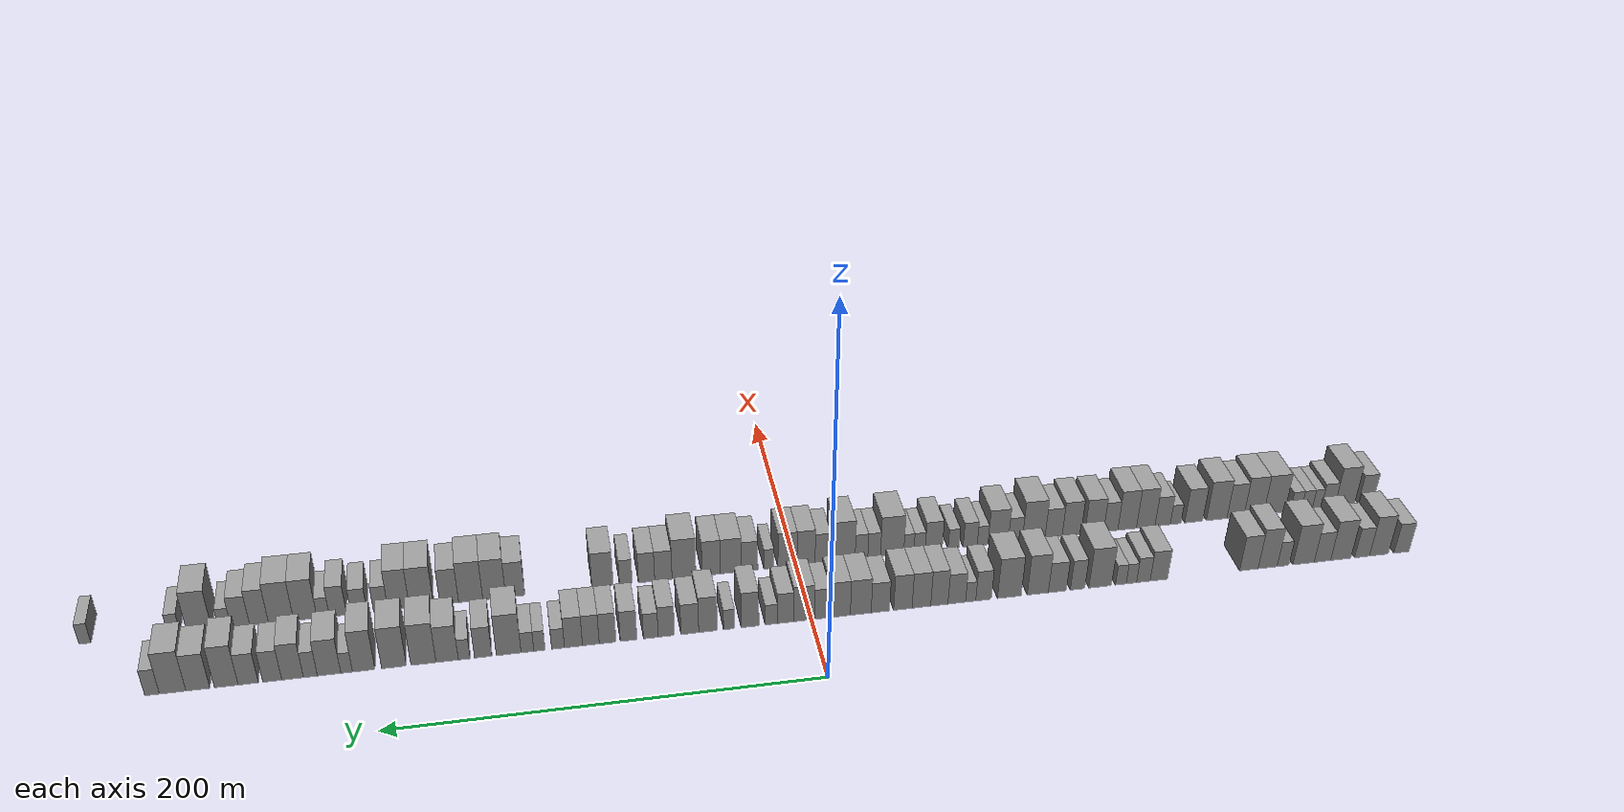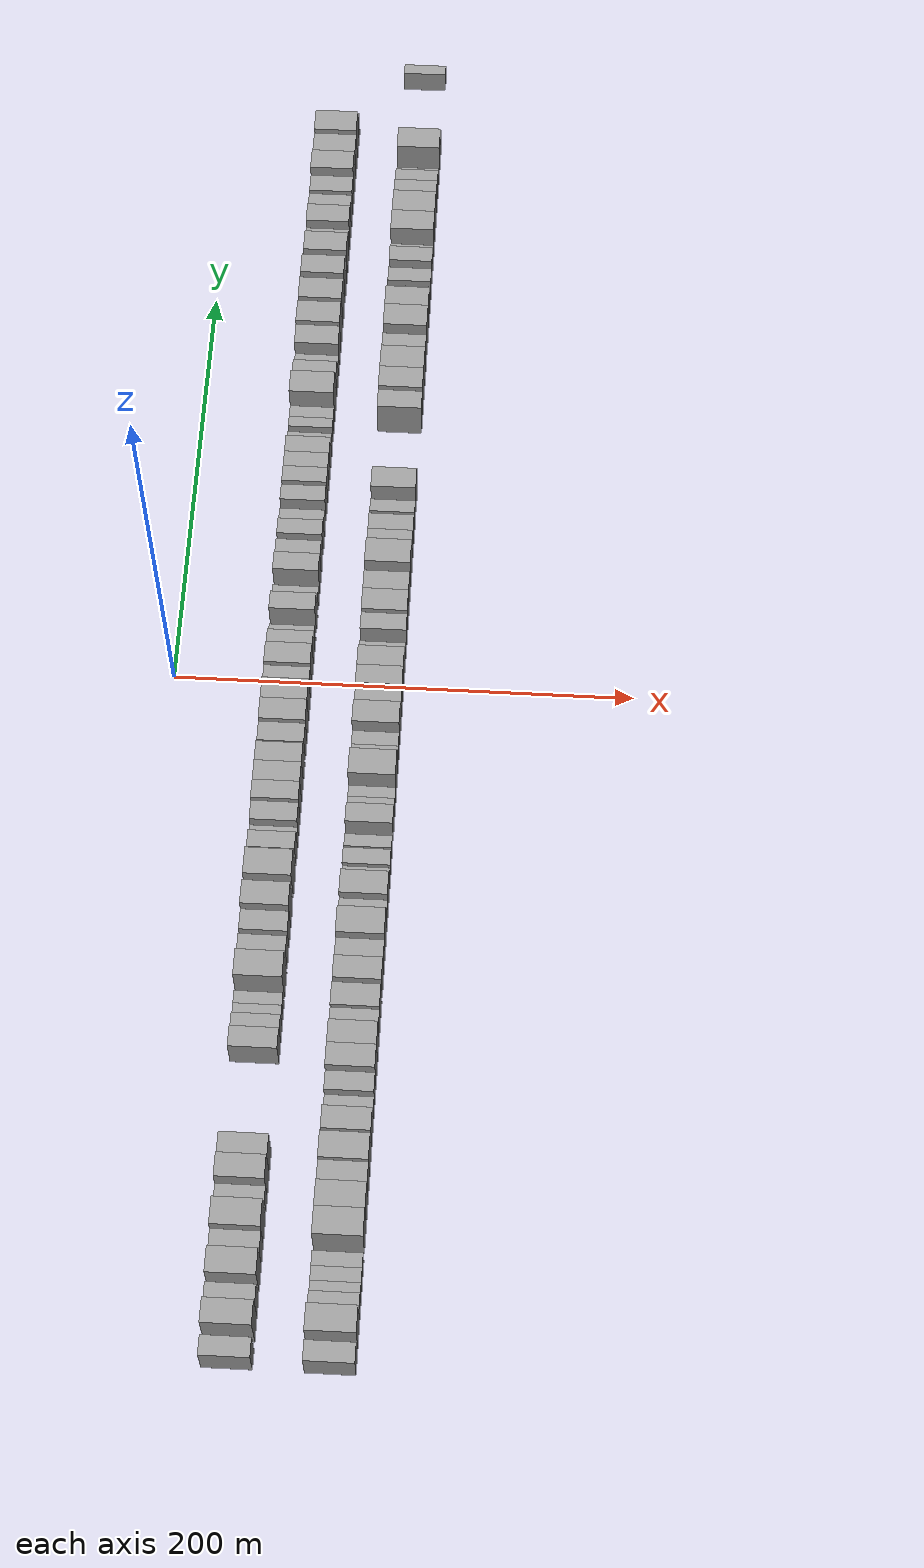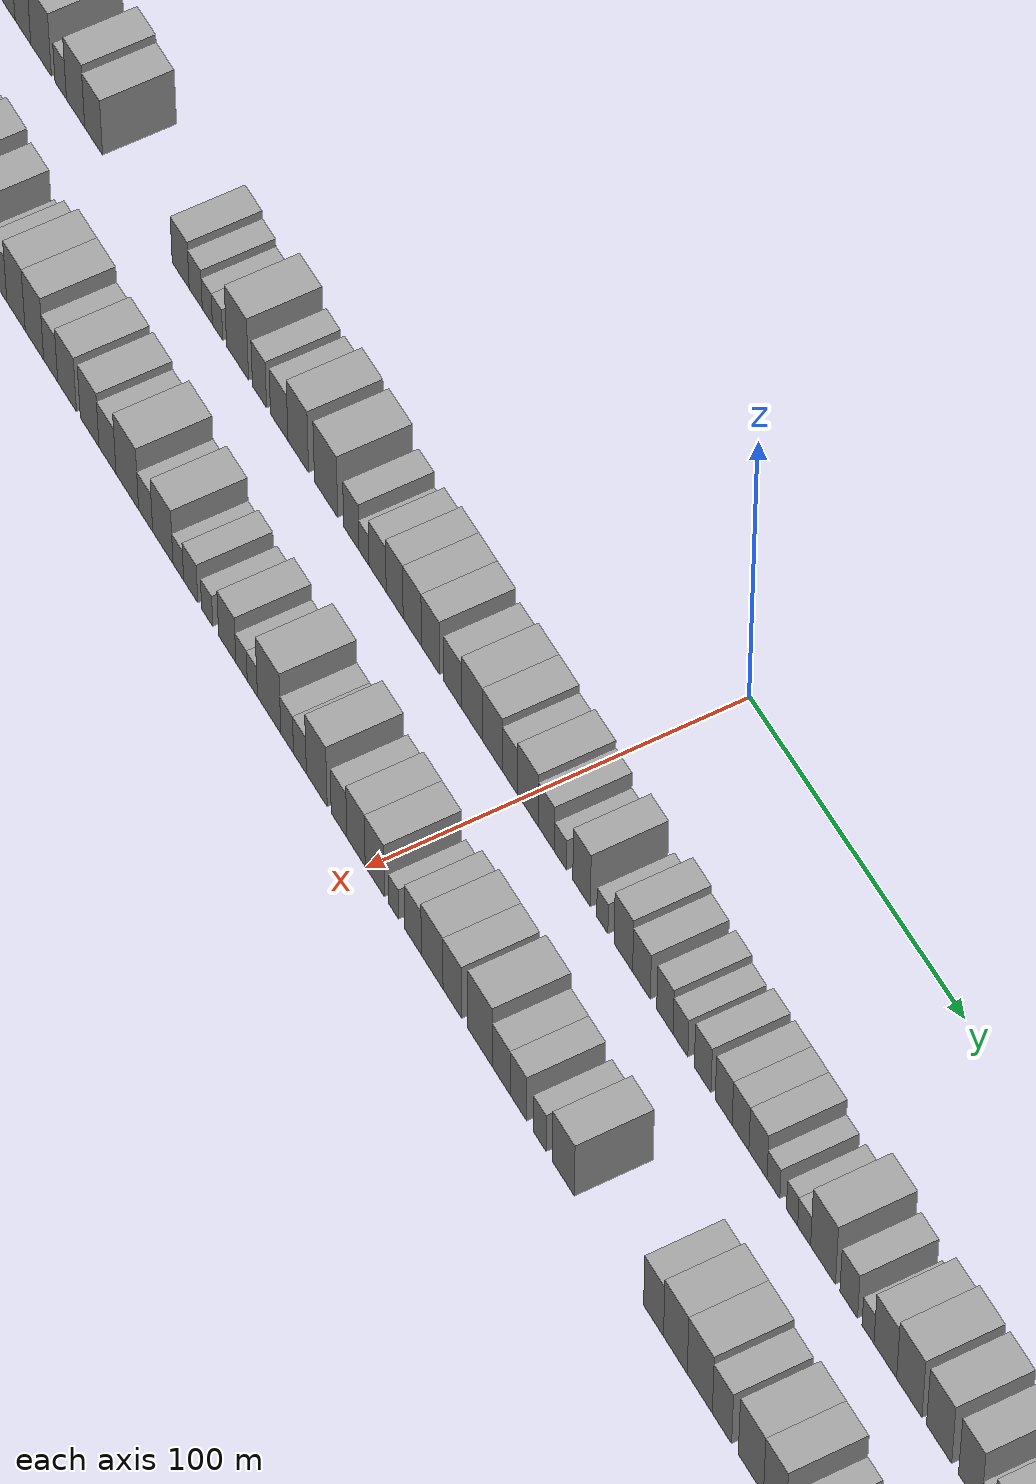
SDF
<sdf version="1.6">
 <world name="default">
  <scene>
   <sky><clouds><speed>12</speed></clouds></sky>
   <ambient>0.4 0.4 0.4 1</ambient>
   <background>0.7 0.7 0.7 1</background>
   <shadows>1</shadows>
  </scene>
  <gravity>0 0 -9.8066</gravity>
  <magnetic_field>6e-06 2.3e-05 -4.2e-05</magnetic_field>
  <physics default="0" name="default_physics" type="ode">
   <ode>
    <solver>
     <type>quick</type>
     <iters>10</iters>
     <sor>1.0</sor>
     <use_dynamic_moi_rescaling>0</use_dynamic_moi_rescaling>
    </solver>
    <constraints>
     <cfm>0</cfm>
     <erp>0.2</erp>
     <contact_max_correcting_vel>100</contact_max_correcting_vel>
     <contact_surface_layer>0.001</contact_surface_layer>
    </constraints>
   </ode>
   <max_step_size>0.004</max_step_size>
   <real_time_factor>1</real_time_factor>
   <real_time_update_rate>250</real_time_update_rate>
  </physics>
  <light name="sun" type="directional">
   <pose>0 0 10 0 0 0</pose>
   <diffuse>0.8 0.8 0.8 1</diffuse>
   <specular>0.2 0.2 0.2 1</specular>
   <attenuation>
    <range>1000</range>
    <constant>0.9</constant>
    <linear>0.01</linear>
    <quadratic>0.001</quadratic>
   </attenuation>
   <direction>-0.5 0.1 -0.9</direction>
  </light>
  <model name="building_1">
   <static>1</static>
   <pose>50.0000 -296.0458 0 0.000000 0.000000 0.000000</pose>
   <link name="link">
    <pose>0 0 9.00 0 0 0</pose>
    <collision name="collision"><geometry><box><size>20.0000 7.9083 18.0000</size></box></geometry></collision>
    <visual name="visual">
     <cast_shadows>0</cast_shadows>
     <geometry><box><size>20.0000 7.9083 18.0000</size></box></geometry>
     <material>
      <script>
       <uri>model://grey_wall/materials/scripts</uri>
       <uri>model://grey_wall/materials/textures</uri>
       <name>vrc/grey_wall</name>
      </script>
     </material>
    </visual>
   </link>
  </model>
  <model name="building_2">
   <static>1</static>
   <pose>50.0000 -284.1533 0 0.000000 0.000000 0.000000</pose>
   <link name="link">
    <pose>0 0 12.00 0 0 0</pose>
    <collision name="collision"><geometry><box><size>20.0000 9.8767 24.0000</size></box></geometry></collision>
    <visual name="visual">
     <cast_shadows>0</cast_shadows>
     <geometry><box><size>20.0000 9.8767 24.0000</size></box></geometry>
     <material>
      <script>
       <uri>model://grey_wall/materials/scripts</uri>
       <uri>model://grey_wall/materials/textures</uri>
       <name>vrc/grey_wall</name>
      </script>
     </material>
    </visual>
   </link>
  </model>
  <model name="building_3">
   <static>1</static>
   <pose>50.0000 -275.3558 0 0.000000 0.000000 0.000000</pose>
   <link name="link">
    <pose>0 0 9.00 0 0 0</pose>
    <collision name="collision"><geometry><box><size>20.0000 7.7183 18.0000</size></box></geometry></collision>
    <visual name="visual">
     <cast_shadows>0</cast_shadows>
     <geometry><box><size>20.0000 7.7183 18.0000</size></box></geometry>
     <material>
      <script>
       <uri>model://grey_wall/materials/scripts</uri>
       <uri>model://grey_wall/materials/textures</uri>
       <name>vrc/grey_wall</name>
      </script>
     </material>
    </visual>
   </link>
  </model>
  <model name="building_4">
   <static>1</static>
   <pose>50.0000 -264.2383 0 0.000000 0.000000 0.000000</pose>
   <link name="link">
    <pose>0 0 12.00 0 0 0</pose>
    <collision name="collision"><geometry><box><size>20.0000 10.5167 24.0000</size></box></geometry></collision>
    <visual name="visual">
     <cast_shadows>0</cast_shadows>
     <geometry><box><size>20.0000 10.5167 24.0000</size></box></geometry>
     <material>
      <script>
       <uri>model://grey_wall/materials/scripts</uri>
       <uri>model://grey_wall/materials/textures</uri>
       <name>vrc/grey_wall</name>
      </script>
     </material>
    </visual>
   </link>
  </model>
  <model name="building_5">
   <static>1</static>
   <pose>50.0000 -254.7254 0 0.000000 0.000000 0.000000</pose>
   <link name="link">
    <pose>0 0 9.00 0 0 0</pose>
    <collision name="collision"><geometry><box><size>20.0000 8.5091 18.0000</size></box></geometry></collision>
    <visual name="visual">
     <cast_shadows>0</cast_shadows>
     <geometry><box><size>20.0000 8.5091 18.0000</size></box></geometry>
     <material>
      <script>
       <uri>model://grey_wall/materials/scripts</uri>
       <uri>model://grey_wall/materials/textures</uri>
       <name>vrc/grey_wall</name>
      </script>
     </material>
    </visual>
   </link>
  </model>
  <model name="building_6">
   <static>1</static>
   <pose>50.0000 -244.9398 0 0.000000 0.000000 0.000000</pose>
   <link name="link">
    <pose>0 0 12.00 0 0 0</pose>
    <collision name="collision"><geometry><box><size>20.0000 11.0621 24.0000</size></box></geometry></collision>
    <visual name="visual">
     <cast_shadows>0</cast_shadows>
     <geometry><box><size>20.0000 11.0621 24.0000</size></box></geometry>
     <material>
      <script>
       <uri>model://grey_wall/materials/scripts</uri>
       <uri>model://grey_wall/materials/textures</uri>
       <name>vrc/grey_wall</name>
      </script>
     </material>
    </visual>
   </link>
  </model>
  <model name="building_7">
   <static>1</static>
   <pose>50.0000 -234.3629 0 0.000000 0.000000 0.000000</pose>
   <link name="link">
    <pose>0 0 7.50 0 0 0</pose>
    <collision name="collision"><geometry><box><size>20.0000 6.0918 15.0000</size></box></geometry></collision>
    <visual name="visual">
     <cast_shadows>0</cast_shadows>
     <geometry><box><size>20.0000 6.0918 15.0000</size></box></geometry>
     <material>
      <script>
       <uri>model://grey_wall/materials/scripts</uri>
       <uri>model://grey_wall/materials/textures</uri>
       <name>vrc/grey_wall</name>
      </script>
     </material>
    </visual>
   </link>
  </model>
  <model name="building_8">
   <static>1</static>
   <pose>50.0000 -226.4206 0 0.000000 0.000000 0.000000</pose>
   <link name="link">
    <pose>0 0 12.00 0 0 0</pose>
    <collision name="collision"><geometry><box><size>20.0000 9.7926 24.0000</size></box></geometry></collision>
    <visual name="visual">
     <cast_shadows>0</cast_shadows>
     <geometry><box><size>20.0000 9.7926 24.0000</size></box></geometry>
     <material>
      <script>
       <uri>model://grey_wall/materials/scripts</uri>
       <uri>model://grey_wall/materials/textures</uri>
       <name>vrc/grey_wall</name>
      </script>
     </material>
    </visual>
   </link>
  </model>
  <model name="building_9">
   <static>1</static>
   <pose>50.0000 -216.7861 0 0.000000 0.000000 0.000000</pose>
   <link name="link">
    <pose>0 0 10.50 0 0 0</pose>
    <collision name="collision"><geometry><box><size>20.0000 9.4765 21.0000</size></box></geometry></collision>
    <visual name="visual">
     <cast_shadows>0</cast_shadows>
     <geometry><box><size>20.0000 9.4765 21.0000</size></box></geometry>
     <material>
      <script>
       <uri>model://grey_wall/materials/scripts</uri>
       <uri>model://grey_wall/materials/textures</uri>
       <name>vrc/grey_wall</name>
      </script>
     </material>
    </visual>
   </link>
  </model>
  <model name="building_10">
   <static>1</static>
   <pose>50.0000 -170.8512 0 0.000000 0.000000 0.000000</pose>
   <link name="link">
    <pose>0 0 9.00 0 0 0</pose>
    <collision name="collision"><geometry><box><size>20.0000 8.7978 18.0000</size></box></geometry></collision>
    <visual name="visual">
     <cast_shadows>0</cast_shadows>
     <geometry><box><size>20.0000 8.7978 18.0000</size></box></geometry>
     <material>
      <script>
       <uri>model://grey_wall/materials/scripts</uri>
       <uri>model://grey_wall/materials/textures</uri>
       <name>vrc/grey_wall</name>
      </script>
     </material>
    </visual>
   </link>
  </model>
  <model name="building_11">
   <static>1</static>
   <pose>50.0000 -163.0367 0 0.000000 0.000000 0.000000</pose>
   <link name="link">
    <pose>0 0 7.50 0 0 0</pose>
    <collision name="collision"><geometry><box><size>20.0000 6.8313 15.0000</size></box></geometry></collision>
    <visual name="visual">
     <cast_shadows>0</cast_shadows>
     <geometry><box><size>20.0000 6.8313 15.0000</size></box></geometry>
     <material>
      <script>
       <uri>model://grey_wall/materials/scripts</uri>
       <uri>model://grey_wall/materials/textures</uri>
       <name>vrc/grey_wall</name>
      </script>
     </material>
    </visual>
   </link>
  </model>
  <model name="building_12">
   <static>1</static>
   <pose>50.0000 -157.0104 0 0.000000 0.000000 0.000000</pose>
   <link name="link">
    <pose>0 0 6.00 0 0 0</pose>
    <collision name="collision"><geometry><box><size>20.0000 5.2213 12.0000</size></box></geometry></collision>
    <visual name="visual">
     <cast_shadows>0</cast_shadows>
     <geometry><box><size>20.0000 5.2213 12.0000</size></box></geometry>
     <material>
      <script>
       <uri>model://grey_wall/materials/scripts</uri>
       <uri>model://grey_wall/materials/textures</uri>
       <name>vrc/grey_wall</name>
      </script>
     </material>
    </visual>
   </link>
  </model>
  <model name="building_13">
   <static>1</static>
   <pose>50.0000 -151.7014 0 0.000000 0.000000 0.000000</pose>
   <link name="link">
    <pose>0 0 6.00 0 0 0</pose>
    <collision name="collision"><geometry><box><size>20.0000 5.3968 12.0000</size></box></geometry></collision>
    <visual name="visual">
     <cast_shadows>0</cast_shadows>
     <geometry><box><size>20.0000 5.3968 12.0000</size></box></geometry>
     <material>
      <script>
       <uri>model://grey_wall/materials/scripts</uri>
       <uri>model://grey_wall/materials/textures</uri>
       <name>vrc/grey_wall</name>
      </script>
     </material>
    </visual>
   </link>
  </model>
  <model name="building_14">
   <static>1</static>
   <pose>50.0000 -141.3305 0 0.000000 0.000000 0.000000</pose>
   <link name="link">
    <pose>0 0 12.00 0 0 0</pose>
    <collision name="collision"><geometry><box><size>20.0000 11.3450 24.0000</size></box></geometry></collision>
    <visual name="visual">
     <cast_shadows>0</cast_shadows>
     <geometry><box><size>20.0000 11.3450 24.0000</size></box></geometry>
     <material>
      <script>
       <uri>model://grey_wall/materials/scripts</uri>
       <uri>model://grey_wall/materials/textures</uri>
       <name>vrc/grey_wall</name>
      </script>
     </material>
    </visual>
   </link>
  </model>
  <model name="building_15">
   <static>1</static>
   <pose>50.0000 -130.0443 0 0.000000 0.000000 0.000000</pose>
   <link name="link">
    <pose>0 0 9.00 0 0 0</pose>
    <collision name="collision"><geometry><box><size>20.0000 7.2274 18.0000</size></box></geometry></collision>
    <visual name="visual">
     <cast_shadows>0</cast_shadows>
     <geometry><box><size>20.0000 7.2274 18.0000</size></box></geometry>
     <material>
      <script>
       <uri>model://grey_wall/materials/scripts</uri>
       <uri>model://grey_wall/materials/textures</uri>
       <name>vrc/grey_wall</name>
      </script>
     </material>
    </visual>
   </link>
  </model>
  <model name="building_16">
   <static>1</static>
   <pose>50.0000 -119.9659 0 0.000000 0.000000 0.000000</pose>
   <link name="link">
    <pose>0 0 9.00 0 0 0</pose>
    <collision name="collision"><geometry><box><size>20.0000 8.9294 18.0000</size></box></geometry></collision>
    <visual name="visual">
     <cast_shadows>0</cast_shadows>
     <geometry><box><size>20.0000 8.9294 18.0000</size></box></geometry>
     <material>
      <script>
       <uri>model://grey_wall/materials/scripts</uri>
       <uri>model://grey_wall/materials/textures</uri>
       <name>vrc/grey_wall</name>
      </script>
     </material>
    </visual>
   </link>
  </model>
  <model name="building_17">
   <static>1</static>
   <pose>50.0000 -110.2654 0 0.000000 0.000000 0.000000</pose>
   <link name="link">
    <pose>0 0 12.00 0 0 0</pose>
    <collision name="collision"><geometry><box><size>20.0000 10.4716 24.0000</size></box></geometry></collision>
    <visual name="visual">
     <cast_shadows>0</cast_shadows>
     <geometry><box><size>20.0000 10.4716 24.0000</size></box></geometry>
     <material>
      <script>
       <uri>model://grey_wall/materials/scripts</uri>
       <uri>model://grey_wall/materials/textures</uri>
       <name>vrc/grey_wall</name>
      </script>
     </material>
    </visual>
   </link>
  </model>
  <model name="building_18">
   <static>1</static>
   <pose>50.0000 -96.1581 0 0.000000 0.000000 0.000000</pose>
   <link name="link">
    <pose>0 0 12.00 0 0 0</pose>
    <collision name="collision"><geometry><box><size>20.0000 11.7430 24.0000</size></box></geometry></collision>
    <visual name="visual">
     <cast_shadows>0</cast_shadows>
     <geometry><box><size>20.0000 11.7430 24.0000</size></box></geometry>
     <material>
      <script>
       <uri>model://grey_wall/materials/scripts</uri>
       <uri>model://grey_wall/materials/textures</uri>
       <name>vrc/grey_wall</name>
      </script>
     </material>
    </visual>
   </link>
  </model>
  <model name="building_19">
   <static>1</static>
   <pose>50.0000 -83.4580 0 0.000000 0.000000 0.000000</pose>
   <link name="link">
    <pose>0 0 9.00 0 0 0</pose>
    <collision name="collision"><geometry><box><size>20.0000 7.6573 18.0000</size></box></geometry></collision>
    <visual name="visual">
     <cast_shadows>0</cast_shadows>
     <geometry><box><size>20.0000 7.6573 18.0000</size></box></geometry>
     <material>
      <script>
       <uri>model://grey_wall/materials/scripts</uri>
       <uri>model://grey_wall/materials/textures</uri>
       <name>vrc/grey_wall</name>
      </script>
     </material>
    </visual>
   </link>
  </model>
  <model name="building_20">
   <static>1</static>
   <pose>50.0000 -77.1153 0 0.000000 0.000000 0.000000</pose>
   <link name="link">
    <pose>0 0 6.00 0 0 0</pose>
    <collision name="collision"><geometry><box><size>20.0000 5.0281 12.0000</size></box></geometry></collision>
    <visual name="visual">
     <cast_shadows>0</cast_shadows>
     <geometry><box><size>20.0000 5.0281 12.0000</size></box></geometry>
     <material>
      <script>
       <uri>model://grey_wall/materials/scripts</uri>
       <uri>model://grey_wall/materials/textures</uri>
       <name>vrc/grey_wall</name>
      </script>
     </material>
    </visual>
   </link>
  </model>
  <model name="building_21">
   <static>1</static>
   <pose>50.0000 -70.3039 0 0.000000 0.000000 0.000000</pose>
   <link name="link">
    <pose>0 0 9.00 0 0 0</pose>
    <collision name="collision"><geometry><box><size>20.0000 8.5948 18.0000</size></box></geometry></collision>
    <visual name="visual">
     <cast_shadows>0</cast_shadows>
     <geometry><box><size>20.0000 8.5948 18.0000</size></box></geometry>
     <material>
      <script>
       <uri>model://grey_wall/materials/scripts</uri>
       <uri>model://grey_wall/materials/textures</uri>
       <name>vrc/grey_wall</name>
      </script>
     </material>
    </visual>
   </link>
  </model>
  <model name="building_22">
   <static>1</static>
   <pose>50.0000 -61.7963 0 0.000000 0.000000 0.000000</pose>
   <link name="link">
    <pose>0 0 10.50 0 0 0</pose>
    <collision name="collision"><geometry><box><size>20.0000 8.4204 21.0000</size></box></geometry></collision>
    <visual name="visual">
     <cast_shadows>0</cast_shadows>
     <geometry><box><size>20.0000 8.4204 21.0000</size></box></geometry>
     <material>
      <script>
       <uri>model://grey_wall/materials/scripts</uri>
       <uri>model://grey_wall/materials/textures</uri>
       <name>vrc/grey_wall</name>
      </script>
     </material>
    </visual>
   </link>
  </model>
  <model name="building_23">
   <static>1</static>
   <pose>50.0000 -53.0342 0 0.000000 0.000000 0.000000</pose>
   <link name="link">
    <pose>0 0 10.50 0 0 0</pose>
    <collision name="collision"><geometry><box><size>20.0000 9.1038 21.0000</size></box></geometry></collision>
    <visual name="visual">
     <cast_shadows>0</cast_shadows>
     <geometry><box><size>20.0000 9.1038 21.0000</size></box></geometry>
     <material>
      <script>
       <uri>model://grey_wall/materials/scripts</uri>
       <uri>model://grey_wall/materials/textures</uri>
       <name>vrc/grey_wall</name>
      </script>
     </material>
    </visual>
   </link>
  </model>
  <model name="building_24">
   <static>1</static>
   <pose>50.0000 -44.0214 0 0.000000 0.000000 0.000000</pose>
   <link name="link">
    <pose>0 0 10.50 0 0 0</pose>
    <collision name="collision"><geometry><box><size>20.0000 8.9219 21.0000</size></box></geometry></collision>
    <visual name="visual">
     <cast_shadows>0</cast_shadows>
     <geometry><box><size>20.0000 8.9219 21.0000</size></box></geometry>
     <material>
      <script>
       <uri>model://grey_wall/materials/scripts</uri>
       <uri>model://grey_wall/materials/textures</uri>
       <name>vrc/grey_wall</name>
      </script>
     </material>
    </visual>
   </link>
  </model>
  <model name="building_25">
   <static>1</static>
   <pose>50.0000 -33.1138 0 0.000000 0.000000 0.000000</pose>
   <link name="link">
    <pose>0 0 9.00 0 0 0</pose>
    <collision name="collision"><geometry><box><size>20.0000 8.8932 18.0000</size></box></geometry></collision>
    <visual name="visual">
     <cast_shadows>0</cast_shadows>
     <geometry><box><size>20.0000 8.8932 18.0000</size></box></geometry>
     <material>
      <script>
       <uri>model://grey_wall/materials/scripts</uri>
       <uri>model://grey_wall/materials/textures</uri>
       <name>vrc/grey_wall</name>
      </script>
     </material>
    </visual>
   </link>
  </model>
  <model name="building_26">
   <static>1</static>
   <pose>50.0000 -23.6485 0 0.000000 0.000000 0.000000</pose>
   <link name="link">
    <pose>0 0 10.50 0 0 0</pose>
    <collision name="collision"><geometry><box><size>20.0000 10.0374 21.0000</size></box></geometry></collision>
    <visual name="visual">
     <cast_shadows>0</cast_shadows>
     <geometry><box><size>20.0000 10.0374 21.0000</size></box></geometry>
     <material>
      <script>
       <uri>model://grey_wall/materials/scripts</uri>
       <uri>model://grey_wall/materials/textures</uri>
       <name>vrc/grey_wall</name>
      </script>
     </material>
    </visual>
   </link>
  </model>
  <model name="building_27">
   <static>1</static>
   <pose>50.0000 -13.7559 0 0.000000 0.000000 0.000000</pose>
   <link name="link">
    <pose>0 0 10.50 0 0 0</pose>
    <collision name="collision"><geometry><box><size>20.0000 9.7480 21.0000</size></box></geometry></collision>
    <visual name="visual">
     <cast_shadows>0</cast_shadows>
     <geometry><box><size>20.0000 9.7480 21.0000</size></box></geometry>
     <material>
      <script>
       <uri>model://grey_wall/materials/scripts</uri>
       <uri>model://grey_wall/materials/textures</uri>
       <name>vrc/grey_wall</name>
      </script>
     </material>
    </visual>
   </link>
  </model>
  <model name="building_28">
   <static>1</static>
   <pose>50.0000 -5.1340 0 0.000000 0.000000 0.000000</pose>
   <link name="link">
    <pose>0 0 9.00 0 0 0</pose>
    <collision name="collision"><geometry><box><size>20.0000 7.4958 18.0000</size></box></geometry></collision>
    <visual name="visual">
     <cast_shadows>0</cast_shadows>
     <geometry><box><size>20.0000 7.4958 18.0000</size></box></geometry>
     <material>
      <script>
       <uri>model://grey_wall/materials/scripts</uri>
       <uri>model://grey_wall/materials/textures</uri>
       <name>vrc/grey_wall</name>
      </script>
     </material>
    </visual>
   </link>
  </model>
  <model name="building_29">
   <static>1</static>
   <pose>50.0000 3.5850 0 0.000000 0.000000 0.000000</pose>
   <link name="link">
    <pose>0 0 10.50 0 0 0</pose>
    <collision name="collision"><geometry><box><size>20.0000 9.9423 21.0000</size></box></geometry></collision>
    <visual name="visual">
     <cast_shadows>0</cast_shadows>
     <geometry><box><size>20.0000 9.9423 21.0000</size></box></geometry>
     <material>
      <script>
       <uri>model://grey_wall/materials/scripts</uri>
       <uri>model://grey_wall/materials/textures</uri>
       <name>vrc/grey_wall</name>
      </script>
     </material>
    </visual>
   </link>
  </model>
  <model name="building_30">
   <static>1</static>
   <pose>50.0000 12.4400 0 0.000000 0.000000 0.000000</pose>
   <link name="link">
    <pose>0 0 9.00 0 0 0</pose>
    <collision name="collision"><geometry><box><size>20.0000 7.7675 18.0000</size></box></geometry></collision>
    <visual name="visual">
     <cast_shadows>0</cast_shadows>
     <geometry><box><size>20.0000 7.7675 18.0000</size></box></geometry>
     <material>
      <script>
       <uri>model://grey_wall/materials/scripts</uri>
       <uri>model://grey_wall/materials/textures</uri>
       <name>vrc/grey_wall</name>
      </script>
     </material>
    </visual>
   </link>
  </model>
  <model name="building_31">
   <static>1</static>
   <pose>50.0000 19.2083 0 0.000000 0.000000 0.000000</pose>
   <link name="link">
    <pose>0 0 6.00 0 0 0</pose>
    <collision name="collision"><geometry><box><size>20.0000 5.7690 12.0000</size></box></geometry></collision>
    <visual name="visual">
     <cast_shadows>0</cast_shadows>
     <geometry><box><size>20.0000 5.7690 12.0000</size></box></geometry>
     <material>
      <script>
       <uri>model://grey_wall/materials/scripts</uri>
       <uri>model://grey_wall/materials/textures</uri>
       <name>vrc/grey_wall</name>
      </script>
     </material>
    </visual>
   </link>
  </model>
  <model name="building_32">
   <static>1</static>
   <pose>50.0000 29.2972 0 0.000000 0.000000 0.000000</pose>
   <link name="link">
    <pose>0 0 10.50 0 0 0</pose>
    <collision name="collision"><geometry><box><size>20.0000 8.4088 21.0000</size></box></geometry></collision>
    <visual name="visual">
     <cast_shadows>0</cast_shadows>
     <geometry><box><size>20.0000 8.4088 21.0000</size></box></geometry>
     <material>
      <script>
       <uri>model://grey_wall/materials/scripts</uri>
       <uri>model://grey_wall/materials/textures</uri>
       <name>vrc/grey_wall</name>
      </script>
     </material>
    </visual>
   </link>
  </model>
  <model name="building_33">
   <static>1</static>
   <pose>50.0000 39.1456 0 0.000000 0.000000 0.000000</pose>
   <link name="link">
    <pose>0 0 6.00 0 0 0</pose>
    <collision name="collision"><geometry><box><size>20.0000 5.2881 12.0000</size></box></geometry></collision>
    <visual name="visual">
     <cast_shadows>0</cast_shadows>
     <geometry><box><size>20.0000 5.2881 12.0000</size></box></geometry>
     <material>
      <script>
       <uri>model://grey_wall/materials/scripts</uri>
       <uri>model://grey_wall/materials/textures</uri>
       <name>vrc/grey_wall</name>
      </script>
     </material>
    </visual>
   </link>
  </model>
  <model name="building_34">
   <static>1</static>
   <pose>50.0000 49.1430 0 0.000000 0.000000 0.000000</pose>
   <link name="link">
    <pose>0 0 10.50 0 0 0</pose>
    <collision name="collision"><geometry><box><size>20.0000 8.7066 21.0000</size></box></geometry></collision>
    <visual name="visual">
     <cast_shadows>0</cast_shadows>
     <geometry><box><size>20.0000 8.7066 21.0000</size></box></geometry>
     <material>
      <script>
       <uri>model://grey_wall/materials/scripts</uri>
       <uri>model://grey_wall/materials/textures</uri>
       <name>vrc/grey_wall</name>
      </script>
     </material>
    </visual>
   </link>
  </model>
  <model name="building_35">
   <static>1</static>
   <pose>50.0000 57.6699 0 0.000000 0.000000 0.000000</pose>
   <link name="link">
    <pose>0 0 9.00 0 0 0</pose>
    <collision name="collision"><geometry><box><size>20.0000 8.3474 18.0000</size></box></geometry></collision>
    <visual name="visual">
     <cast_shadows>0</cast_shadows>
     <geometry><box><size>20.0000 8.3474 18.0000</size></box></geometry>
     <material>
      <script>
       <uri>model://grey_wall/materials/scripts</uri>
       <uri>model://grey_wall/materials/textures</uri>
       <name>vrc/grey_wall</name>
      </script>
     </material>
    </visual>
   </link>
  </model>
  <model name="building_36">
   <static>1</static>
   <pose>50.0000 68.6641 0 0.000000 0.000000 0.000000</pose>
   <link name="link">
    <pose>0 0 9.00 0 0 0</pose>
    <collision name="collision"><geometry><box><size>20.0000 7.6409 18.0000</size></box></geometry></collision>
    <visual name="visual">
     <cast_shadows>0</cast_shadows>
     <geometry><box><size>20.0000 7.6409 18.0000</size></box></geometry>
     <material>
      <script>
       <uri>model://grey_wall/materials/scripts</uri>
       <uri>model://grey_wall/materials/textures</uri>
       <name>vrc/grey_wall</name>
      </script>
     </material>
    </visual>
   </link>
  </model>
  <model name="building_37">
   <static>1</static>
   <pose>50.0000 75.9450 0 0.000000 0.000000 0.000000</pose>
   <link name="link">
    <pose>0 0 7.50 0 0 0</pose>
    <collision name="collision"><geometry><box><size>20.0000 6.9210 15.0000</size></box></geometry></collision>
    <visual name="visual">
     <cast_shadows>0</cast_shadows>
     <geometry><box><size>20.0000 6.9210 15.0000</size></box></geometry>
     <material>
      <script>
       <uri>model://grey_wall/materials/scripts</uri>
       <uri>model://grey_wall/materials/textures</uri>
       <name>vrc/grey_wall</name>
      </script>
     </material>
    </visual>
   </link>
  </model>
  <model name="building_38">
   <static>1</static>
   <pose>50.0000 86.2765 0 0.000000 0.000000 0.000000</pose>
   <link name="link">
    <pose>0 0 9.00 0 0 0</pose>
    <collision name="collision"><geometry><box><size>20.0000 7.7419 18.0000</size></box></geometry></collision>
    <visual name="visual">
     <cast_shadows>0</cast_shadows>
     <geometry><box><size>20.0000 7.7419 18.0000</size></box></geometry>
     <material>
      <script>
       <uri>model://grey_wall/materials/scripts</uri>
       <uri>model://grey_wall/materials/textures</uri>
       <name>vrc/grey_wall</name>
      </script>
     </material>
    </visual>
   </link>
  </model>
  <model name="building_39">
   <static>1</static>
   <pose>50.0000 96.0376 0 0.000000 0.000000 0.000000</pose>
   <link name="link">
    <pose>0 0 9.00 0 0 0</pose>
    <collision name="collision"><geometry><box><size>20.0000 7.7805 18.0000</size></box></geometry></collision>
    <visual name="visual">
     <cast_shadows>0</cast_shadows>
     <geometry><box><size>20.0000 7.7805 18.0000</size></box></geometry>
     <material>
      <script>
       <uri>model://grey_wall/materials/scripts</uri>
       <uri>model://grey_wall/materials/textures</uri>
       <name>vrc/grey_wall</name>
      </script>
     </material>
    </visual>
   </link>
  </model>
  <model name="building_40">
   <static>1</static>
   <pose>50.0000 103.7960 0 0.000000 0.000000 0.000000</pose>
   <link name="link">
    <pose>0 0 9.00 0 0 0</pose>
    <collision name="collision"><geometry><box><size>20.0000 7.7362 18.0000</size></box></geometry></collision>
    <visual name="visual">
     <cast_shadows>0</cast_shadows>
     <geometry><box><size>20.0000 7.7362 18.0000</size></box></geometry>
     <material>
      <script>
       <uri>model://grey_wall/materials/scripts</uri>
       <uri>model://grey_wall/materials/textures</uri>
       <name>vrc/grey_wall</name>
      </script>
     </material>
    </visual>
   </link>
  </model>
  <model name="building_41">
   <static>1</static>
   <pose>50.0000 111.8288 0 0.000000 0.000000 0.000000</pose>
   <link name="link">
    <pose>0 0 9.00 0 0 0</pose>
    <collision name="collision"><geometry><box><size>20.0000 8.3295 18.0000</size></box></geometry></collision>
    <visual name="visual">
     <cast_shadows>0</cast_shadows>
     <geometry><box><size>20.0000 8.3295 18.0000</size></box></geometry>
     <material>
      <script>
       <uri>model://grey_wall/materials/scripts</uri>
       <uri>model://grey_wall/materials/textures</uri>
       <name>vrc/grey_wall</name>
      </script>
     </material>
    </visual>
   </link>
  </model>
  <model name="building_42">
   <static>1</static>
   <pose>50.0000 118.9388 0 0.000000 0.000000 0.000000</pose>
   <link name="link">
    <pose>0 0 6.00 0 0 0</pose>
    <collision name="collision"><geometry><box><size>20.0000 5.8905 12.0000</size></box></geometry></collision>
    <visual name="visual">
     <cast_shadows>0</cast_shadows>
     <geometry><box><size>20.0000 5.8905 12.0000</size></box></geometry>
     <material>
      <script>
       <uri>model://grey_wall/materials/scripts</uri>
       <uri>model://grey_wall/materials/textures</uri>
       <name>vrc/grey_wall</name>
      </script>
     </material>
    </visual>
   </link>
  </model>
  <model name="building_43">
   <static>1</static>
   <pose>50.0000 127.4671 0 0.000000 0.000000 0.000000</pose>
   <link name="link">
    <pose>0 0 6.00 0 0 0</pose>
    <collision name="collision"><geometry><box><size>20.0000 5.1661 12.0000</size></box></geometry></collision>
    <visual name="visual">
     <cast_shadows>0</cast_shadows>
     <geometry><box><size>20.0000 5.1661 12.0000</size></box></geometry>
     <material>
      <script>
       <uri>model://grey_wall/materials/scripts</uri>
       <uri>model://grey_wall/materials/textures</uri>
       <name>vrc/grey_wall</name>
      </script>
     </material>
    </visual>
   </link>
  </model>
  <model name="building_44">
   <static>1</static>
   <pose>50.0000 132.9723 0 0.000000 0.000000 0.000000</pose>
   <link name="link">
    <pose>0 0 6.00 0 0 0</pose>
    <collision name="collision"><geometry><box><size>20.0000 5.8444 12.0000</size></box></geometry></collision>
    <visual name="visual">
     <cast_shadows>0</cast_shadows>
     <geometry><box><size>20.0000 5.8444 12.0000</size></box></geometry>
     <material>
      <script>
       <uri>model://grey_wall/materials/scripts</uri>
       <uri>model://grey_wall/materials/textures</uri>
       <name>vrc/grey_wall</name>
      </script>
     </material>
    </visual>
   </link>
  </model>
  <model name="building_45">
   <static>1</static>
   <pose>50.0000 141.5381 0 0.000000 0.000000 0.000000</pose>
   <link name="link">
    <pose>0 0 12.00 0 0 0</pose>
    <collision name="collision"><geometry><box><size>20.0000 11.2872 24.0000</size></box></geometry></collision>
    <visual name="visual">
     <cast_shadows>0</cast_shadows>
     <geometry><box><size>20.0000 11.2872 24.0000</size></box></geometry>
     <material>
      <script>
       <uri>model://grey_wall/materials/scripts</uri>
       <uri>model://grey_wall/materials/textures</uri>
       <name>vrc/grey_wall</name>
      </script>
     </material>
    </visual>
   </link>
  </model>
  <model name="building_46">
   <static>1</static>
   <pose>50.0000 153.1510 0 0.000000 0.000000 0.000000</pose>
   <link name="link">
    <pose>0 0 9.00 0 0 0</pose>
    <collision name="collision"><geometry><box><size>20.0000 7.9388 18.0000</size></box></geometry></collision>
    <visual name="visual">
     <cast_shadows>0</cast_shadows>
     <geometry><box><size>20.0000 7.9388 18.0000</size></box></geometry>
     <material>
      <script>
       <uri>model://grey_wall/materials/scripts</uri>
       <uri>model://grey_wall/materials/textures</uri>
       <name>vrc/grey_wall</name>
      </script>
     </material>
    </visual>
   </link>
  </model>
  <model name="building_47">
   <static>1</static>
   <pose>50.0000 161.8052 0 0.000000 0.000000 0.000000</pose>
   <link name="link">
    <pose>0 0 6.00 0 0 0</pose>
    <collision name="collision"><geometry><box><size>20.0000 5.3695 12.0000</size></box></geometry></collision>
    <visual name="visual">
     <cast_shadows>0</cast_shadows>
     <geometry><box><size>20.0000 5.3695 12.0000</size></box></geometry>
     <material>
      <script>
       <uri>model://grey_wall/materials/scripts</uri>
       <uri>model://grey_wall/materials/textures</uri>
       <name>vrc/grey_wall</name>
      </script>
     </material>
    </visual>
   </link>
  </model>
  <model name="building_48">
   <static>1</static>
   <pose>50.0000 169.5422 0 0.000000 0.000000 0.000000</pose>
   <link name="link">
    <pose>0 0 10.50 0 0 0</pose>
    <collision name="collision"><geometry><box><size>20.0000 10.1045 21.0000</size></box></geometry></collision>
    <visual name="visual">
     <cast_shadows>0</cast_shadows>
     <geometry><box><size>20.0000 10.1045 21.0000</size></box></geometry>
     <material>
      <script>
       <uri>model://grey_wall/materials/scripts</uri>
       <uri>model://grey_wall/materials/textures</uri>
       <name>vrc/grey_wall</name>
      </script>
     </material>
    </visual>
   </link>
  </model>
  <model name="building_49">
   <static>1</static>
   <pose>50.0000 180.2540 0 0.000000 0.000000 0.000000</pose>
   <link name="link">
    <pose>0 0 12.00 0 0 0</pose>
    <collision name="collision"><geometry><box><size>20.0000 11.3189 24.0000</size></box></geometry></collision>
    <visual name="visual">
     <cast_shadows>0</cast_shadows>
     <geometry><box><size>20.0000 11.3189 24.0000</size></box></geometry>
     <material>
      <script>
       <uri>model://grey_wall/materials/scripts</uri>
       <uri>model://grey_wall/materials/textures</uri>
       <name>vrc/grey_wall</name>
      </script>
     </material>
    </visual>
   </link>
  </model>
  <model name="building_50">
   <static>1</static>
   <pose>50.0000 193.4808 0 0.000000 0.000000 0.000000</pose>
   <link name="link">
    <pose>0 0 12.00 0 0 0</pose>
    <collision name="collision"><geometry><box><size>20.0000 11.1347 24.0000</size></box></geometry></collision>
    <visual name="visual">
     <cast_shadows>0</cast_shadows>
     <geometry><box><size>20.0000 11.1347 24.0000</size></box></geometry>
     <material>
      <script>
       <uri>model://grey_wall/materials/scripts</uri>
       <uri>model://grey_wall/materials/textures</uri>
       <name>vrc/grey_wall</name>
      </script>
     </material>
    </visual>
   </link>
  </model>
  <model name="building_51">
   <static>1</static>
   <pose>50.0000 207.0687 0 0.000000 0.000000 0.000000</pose>
   <link name="link">
    <pose>0 0 12.00 0 0 0</pose>
    <collision name="collision"><geometry><box><size>20.0000 10.0411 24.0000</size></box></geometry></collision>
    <visual name="visual">
     <cast_shadows>0</cast_shadows>
     <geometry><box><size>20.0000 10.0411 24.0000</size></box></geometry>
     <material>
      <script>
       <uri>model://grey_wall/materials/scripts</uri>
       <uri>model://grey_wall/materials/textures</uri>
       <name>vrc/grey_wall</name>
      </script>
     </material>
    </visual>
   </link>
  </model>
  <model name="building_52">
   <static>1</static>
   <pose>50.0000 214.6872 0 0.000000 0.000000 0.000000</pose>
   <link name="link">
    <pose>0 0 6.00 0 0 0</pose>
    <collision name="collision"><geometry><box><size>20.0000 5.1960 12.0000</size></box></geometry></collision>
    <visual name="visual">
     <cast_shadows>0</cast_shadows>
     <geometry><box><size>20.0000 5.1960 12.0000</size></box></geometry>
     <material>
      <script>
       <uri>model://grey_wall/materials/scripts</uri>
       <uri>model://grey_wall/materials/textures</uri>
       <name>vrc/grey_wall</name>
      </script>
     </material>
    </visual>
   </link>
  </model>
  <model name="building_53">
   <static>1</static>
   <pose>50.0000 222.4880 0 0.000000 0.000000 0.000000</pose>
   <link name="link">
    <pose>0 0 10.50 0 0 0</pose>
    <collision name="collision"><geometry><box><size>20.0000 10.4055 21.0000</size></box></geometry></collision>
    <visual name="visual">
     <cast_shadows>0</cast_shadows>
     <geometry><box><size>20.0000 10.4055 21.0000</size></box></geometry>
     <material>
      <script>
       <uri>model://grey_wall/materials/scripts</uri>
       <uri>model://grey_wall/materials/textures</uri>
       <name>vrc/grey_wall</name>
      </script>
     </material>
    </visual>
   </link>
  </model>
  <model name="building_54">
   <static>1</static>
   <pose>50.0000 230.7958 0 0.000000 0.000000 0.000000</pose>
   <link name="link">
    <pose>0 0 7.50 0 0 0</pose>
    <collision name="collision"><geometry><box><size>20.0000 6.2102 15.0000</size></box></geometry></collision>
    <visual name="visual">
     <cast_shadows>0</cast_shadows>
     <geometry><box><size>20.0000 6.2102 15.0000</size></box></geometry>
     <material>
      <script>
       <uri>model://grey_wall/materials/scripts</uri>
       <uri>model://grey_wall/materials/textures</uri>
       <name>vrc/grey_wall</name>
      </script>
     </material>
    </visual>
   </link>
  </model>
  <model name="building_55">
   <static>1</static>
   <pose>50.0000 238.6877 0 0.000000 0.000000 0.000000</pose>
   <link name="link">
    <pose>0 0 10.50 0 0 0</pose>
    <collision name="collision"><geometry><box><size>20.0000 9.5736 21.0000</size></box></geometry></collision>
    <visual name="visual">
     <cast_shadows>0</cast_shadows>
     <geometry><box><size>20.0000 9.5736 21.0000</size></box></geometry>
     <material>
      <script>
       <uri>model://grey_wall/materials/scripts</uri>
       <uri>model://grey_wall/materials/textures</uri>
       <name>vrc/grey_wall</name>
      </script>
     </material>
    </visual>
   </link>
  </model>
  <model name="building_56">
   <static>1</static>
   <pose>50.0000 247.6380 0 0.000000 0.000000 0.000000</pose>
   <link name="link">
    <pose>0 0 9.00 0 0 0</pose>
    <collision name="collision"><geometry><box><size>20.0000 8.3271 18.0000</size></box></geometry></collision>
    <visual name="visual">
     <cast_shadows>0</cast_shadows>
     <geometry><box><size>20.0000 8.3271 18.0000</size></box></geometry>
     <material>
      <script>
       <uri>model://grey_wall/materials/scripts</uri>
       <uri>model://grey_wall/materials/textures</uri>
       <name>vrc/grey_wall</name>
      </script>
     </material>
    </visual>
   </link>
  </model>
  <model name="building_57">
   <static>1</static>
   <pose>50.0000 258.2415 0 0.000000 0.000000 0.000000</pose>
   <link name="link">
    <pose>0 0 9.00 0 0 0</pose>
    <collision name="collision"><geometry><box><size>20.0000 8.8799 18.0000</size></box></geometry></collision>
    <visual name="visual">
     <cast_shadows>0</cast_shadows>
     <geometry><box><size>20.0000 8.8799 18.0000</size></box></geometry>
     <material>
      <script>
       <uri>model://grey_wall/materials/scripts</uri>
       <uri>model://grey_wall/materials/textures</uri>
       <name>vrc/grey_wall</name>
      </script>
     </material>
    </visual>
   </link>
  </model>
  <model name="building_58">
   <static>1</static>
   <pose>50.0000 267.8703 0 0.000000 0.000000 0.000000</pose>
   <link name="link">
    <pose>0 0 12.00 0 0 0</pose>
    <collision name="collision"><geometry><box><size>20.0000 10.3775 24.0000</size></box></geometry></collision>
    <visual name="visual">
     <cast_shadows>0</cast_shadows>
     <geometry><box><size>20.0000 10.3775 24.0000</size></box></geometry>
     <material>
      <script>
       <uri>model://grey_wall/materials/scripts</uri>
       <uri>model://grey_wall/materials/textures</uri>
       <name>vrc/grey_wall</name>
      </script>
     </material>
    </visual>
   </link>
  </model>
  <model name="building_59">
   <static>1</static>
   <pose>50.0000 280.2783 0 0.000000 0.000000 0.000000</pose>
   <link name="link">
    <pose>0 0 10.50 0 0 0</pose>
    <collision name="collision"><geometry><box><size>20.0000 10.4386 21.0000</size></box></geometry></collision>
    <visual name="visual">
     <cast_shadows>0</cast_shadows>
     <geometry><box><size>20.0000 10.4386 21.0000</size></box></geometry>
     <material>
      <script>
       <uri>model://grey_wall/materials/scripts</uri>
       <uri>model://grey_wall/materials/textures</uri>
       <name>vrc/grey_wall</name>
      </script>
     </material>
    </visual>
   </link>
  </model>
  <model name="building_60">
   <static>1</static>
   <pose>50.0000 291.2309 0 0.000000 0.000000 0.000000</pose>
   <link name="link">
    <pose>0 0 12.00 0 0 0</pose>
    <collision name="collision"><geometry><box><size>20.0000 11.4666 24.0000</size></box></geometry></collision>
    <visual name="visual">
     <cast_shadows>0</cast_shadows>
     <geometry><box><size>20.0000 11.4666 24.0000</size></box></geometry>
     <material>
      <script>
       <uri>model://grey_wall/materials/scripts</uri>
       <uri>model://grey_wall/materials/textures</uri>
       <name>vrc/grey_wall</name>
      </script>
     </material>
    </visual>
   </link>
  </model>
  <model name="building_61">
   <static>1</static>
   <pose>50.0000 300.1494 0 0.000000 0.000000 0.000000</pose>
   <link name="link">
    <pose>0 0 7.50 0 0 0</pose>
    <collision name="collision"><geometry><box><size>20.0000 6.3704 15.0000</size></box></geometry></collision>
    <visual name="visual">
     <cast_shadows>0</cast_shadows>
     <geometry><box><size>20.0000 6.3704 15.0000</size></box></geometry>
     <material>
      <script>
       <uri>model://grey_wall/materials/scripts</uri>
       <uri>model://grey_wall/materials/textures</uri>
       <name>vrc/grey_wall</name>
      </script>
     </material>
    </visual>
   </link>
  </model>
  <model name="building_62">
   <static>1</static>
   <pose>90.0000 -295.9540 0 0.000000 0.000000 0.000000</pose>
   <link name="link">
    <pose>0 0 9.00 0 0 0</pose>
    <collision name="collision"><geometry><box><size>20.0000 8.0920 18.0000</size></box></geometry></collision>
    <visual name="visual">
     <cast_shadows>0</cast_shadows>
     <geometry><box><size>20.0000 8.0920 18.0000</size></box></geometry>
     <material>
      <script>
       <uri>model://grey_wall/materials/scripts</uri>
       <uri>model://grey_wall/materials/textures</uri>
       <name>vrc/grey_wall</name>
      </script>
     </material>
    </visual>
   </link>
  </model>
  <model name="building_63">
   <static>1</static>
   <pose>90.0000 -284.5752 0 0.000000 0.000000 0.000000</pose>
   <link name="link">
    <pose>0 0 12.00 0 0 0</pose>
    <collision name="collision"><geometry><box><size>20.0000 10.6655 24.0000</size></box></geometry></collision>
    <visual name="visual">
     <cast_shadows>0</cast_shadows>
     <geometry><box><size>20.0000 10.6655 24.0000</size></box></geometry>
     <material>
      <script>
       <uri>model://grey_wall/materials/scripts</uri>
       <uri>model://grey_wall/materials/textures</uri>
       <name>vrc/grey_wall</name>
      </script>
     </material>
    </visual>
   </link>
  </model>
  <model name="building_64">
   <static>1</static>
   <pose>90.0000 -275.5904 0 0.000000 0.000000 0.000000</pose>
   <link name="link">
    <pose>0 0 7.50 0 0 0</pose>
    <collision name="collision"><geometry><box><size>20.0000 7.3041 15.0000</size></box></geometry></collision>
    <visual name="visual">
     <cast_shadows>0</cast_shadows>
     <geometry><box><size>20.0000 7.3041 15.0000</size></box></geometry>
     <material>
      <script>
       <uri>model://grey_wall/materials/scripts</uri>
       <uri>model://grey_wall/materials/textures</uri>
       <name>vrc/grey_wall</name>
      </script>
     </material>
    </visual>
   </link>
  </model>
  <model name="building_65">
   <static>1</static>
   <pose>90.0000 -269.4973 0 0.000000 0.000000 0.000000</pose>
   <link name="link">
    <pose>0 0 6.00 0 0 0</pose>
    <collision name="collision"><geometry><box><size>20.0000 4.8821 12.0000</size></box></geometry></collision>
    <visual name="visual">
     <cast_shadows>0</cast_shadows>
     <geometry><box><size>20.0000 4.8821 12.0000</size></box></geometry>
     <material>
      <script>
       <uri>model://grey_wall/materials/scripts</uri>
       <uri>model://grey_wall/materials/textures</uri>
       <name>vrc/grey_wall</name>
      </script>
     </material>
    </visual>
   </link>
  </model>
  <model name="building_66">
   <static>1</static>
   <pose>90.0000 -264.1285 0 0.000000 0.000000 0.000000</pose>
   <link name="link">
    <pose>0 0 6.00 0 0 0</pose>
    <collision name="collision"><geometry><box><size>20.0000 5.8553 12.0000</size></box></geometry></collision>
    <visual name="visual">
     <cast_shadows>0</cast_shadows>
     <geometry><box><size>20.0000 5.8553 12.0000</size></box></geometry>
     <material>
      <script>
       <uri>model://grey_wall/materials/scripts</uri>
       <uri>model://grey_wall/materials/textures</uri>
       <name>vrc/grey_wall</name>
      </script>
     </material>
    </visual>
   </link>
  </model>
  <model name="building_67">
   <static>1</static>
   <pose>90.0000 -258.2167 0 0.000000 0.000000 0.000000</pose>
   <link name="link">
    <pose>0 0 6.00 0 0 0</pose>
    <collision name="collision"><geometry><box><size>20.0000 5.9683 12.0000</size></box></geometry></collision>
    <visual name="visual">
     <cast_shadows>0</cast_shadows>
     <geometry><box><size>20.0000 5.9683 12.0000</size></box></geometry>
     <material>
      <script>
       <uri>model://grey_wall/materials/scripts</uri>
       <uri>model://grey_wall/materials/textures</uri>
       <name>vrc/grey_wall</name>
      </script>
     </material>
    </visual>
   </link>
  </model>
  <model name="building_68">
   <static>1</static>
   <pose>90.0000 -246.5864 0 0.000000 0.000000 0.000000</pose>
   <link name="link">
    <pose>0 0 12.00 0 0 0</pose>
    <collision name="collision"><geometry><box><size>20.0000 11.2924 24.0000</size></box></geometry></collision>
    <visual name="visual">
     <cast_shadows>0</cast_shadows>
     <geometry><box><size>20.0000 11.2924 24.0000</size></box></geometry>
     <material>
      <script>
       <uri>model://grey_wall/materials/scripts</uri>
       <uri>model://grey_wall/materials/textures</uri>
       <name>vrc/grey_wall</name>
      </script>
     </material>
    </visual>
   </link>
  </model>
  <model name="building_69">
   <static>1</static>
   <pose>90.0000 -235.6654 0 0.000000 0.000000 0.000000</pose>
   <link name="link">
    <pose>0 0 12.00 0 0 0</pose>
    <collision name="collision"><geometry><box><size>20.0000 10.5495 24.0000</size></box></geometry></collision>
    <visual name="visual">
     <cast_shadows>0</cast_shadows>
     <geometry><box><size>20.0000 10.5495 24.0000</size></box></geometry>
     <material>
      <script>
       <uri>model://grey_wall/materials/scripts</uri>
       <uri>model://grey_wall/materials/textures</uri>
       <name>vrc/grey_wall</name>
      </script>
     </material>
    </visual>
   </link>
  </model>
  <model name="building_70">
   <static>1</static>
   <pose>90.0000 -225.9069 0 0.000000 0.000000 0.000000</pose>
   <link name="link">
    <pose>0 0 10.50 0 0 0</pose>
    <collision name="collision"><geometry><box><size>20.0000 8.9675 21.0000</size></box></geometry></collision>
    <visual name="visual">
     <cast_shadows>0</cast_shadows>
     <geometry><box><size>20.0000 8.9675 21.0000</size></box></geometry>
     <material>
      <script>
       <uri>model://grey_wall/materials/scripts</uri>
       <uri>model://grey_wall/materials/textures</uri>
       <name>vrc/grey_wall</name>
      </script>
     </material>
    </visual>
   </link>
  </model>
  <model name="building_71">
   <static>1</static>
   <pose>90.0000 -215.9592 0 0.000000 0.000000 0.000000</pose>
   <link name="link">
    <pose>0 0 12.00 0 0 0</pose>
    <collision name="collision"><geometry><box><size>20.0000 10.9280 24.0000</size></box></geometry></collision>
    <visual name="visual">
     <cast_shadows>0</cast_shadows>
     <geometry><box><size>20.0000 10.9280 24.0000</size></box></geometry>
     <material>
      <script>
       <uri>model://grey_wall/materials/scripts</uri>
       <uri>model://grey_wall/materials/textures</uri>
       <name>vrc/grey_wall</name>
      </script>
     </material>
    </visual>
   </link>
  </model>
  <model name="building_72">
   <static>1</static>
   <pose>90.0000 -203.7494 0 0.000000 0.000000 0.000000</pose>
   <link name="link">
    <pose>0 0 10.50 0 0 0</pose>
    <collision name="collision"><geometry><box><size>20.0000 9.4916 21.0000</size></box></geometry></collision>
    <visual name="visual">
     <cast_shadows>0</cast_shadows>
     <geometry><box><size>20.0000 9.4916 21.0000</size></box></geometry>
     <material>
      <script>
       <uri>model://grey_wall/materials/scripts</uri>
       <uri>model://grey_wall/materials/textures</uri>
       <name>vrc/grey_wall</name>
      </script>
     </material>
    </visual>
   </link>
  </model>
  <model name="building_73">
   <static>1</static>
   <pose>90.0000 -194.1893 0 0.000000 0.000000 0.000000</pose>
   <link name="link">
    <pose>0 0 6.00 0 0 0</pose>
    <collision name="collision"><geometry><box><size>20.0000 5.6286 12.0000</size></box></geometry></collision>
    <visual name="visual">
     <cast_shadows>0</cast_shadows>
     <geometry><box><size>20.0000 5.6286 12.0000</size></box></geometry>
     <material>
      <script>
       <uri>model://grey_wall/materials/scripts</uri>
       <uri>model://grey_wall/materials/textures</uri>
       <name>vrc/grey_wall</name>
      </script>
     </material>
    </visual>
   </link>
  </model>
  <model name="building_74">
   <static>1</static>
   <pose>90.0000 -187.3581 0 0.000000 0.000000 0.000000</pose>
   <link name="link">
    <pose>0 0 9.00 0 0 0</pose>
    <collision name="collision"><geometry><box><size>20.0000 8.0338 18.0000</size></box></geometry></collision>
    <visual name="visual">
     <cast_shadows>0</cast_shadows>
     <geometry><box><size>20.0000 8.0338 18.0000</size></box></geometry>
     <material>
      <script>
       <uri>model://grey_wall/materials/scripts</uri>
       <uri>model://grey_wall/materials/textures</uri>
       <name>vrc/grey_wall</name>
      </script>
     </material>
    </visual>
   </link>
  </model>
  <model name="building_75">
   <static>1</static>
   <pose>90.0000 -178.4802 0 0.000000 0.000000 0.000000</pose>
   <link name="link">
    <pose>0 0 12.00 0 0 0</pose>
    <collision name="collision"><geometry><box><size>20.0000 9.7219 24.0000</size></box></geometry></collision>
    <visual name="visual">
     <cast_shadows>0</cast_shadows>
     <geometry><box><size>20.0000 9.7219 24.0000</size></box></geometry>
     <material>
      <script>
       <uri>model://grey_wall/materials/scripts</uri>
       <uri>model://grey_wall/materials/textures</uri>
       <name>vrc/grey_wall</name>
      </script>
     </material>
    </visual>
   </link>
  </model>
  <model name="building_76">
   <static>1</static>
   <pose>90.0000 -168.7378 0 0.000000 0.000000 0.000000</pose>
   <link name="link">
    <pose>0 0 12.00 0 0 0</pose>
    <collision name="collision"><geometry><box><size>20.0000 9.7629 24.0000</size></box></geometry></collision>
    <visual name="visual">
     <cast_shadows>0</cast_shadows>
     <geometry><box><size>20.0000 9.7629 24.0000</size></box></geometry>
     <material>
      <script>
       <uri>model://grey_wall/materials/scripts</uri>
       <uri>model://grey_wall/materials/textures</uri>
       <name>vrc/grey_wall</name>
      </script>
     </material>
    </visual>
   </link>
  </model>
  <model name="building_77">
   <static>1</static>
   <pose>90.0000 -160.1544 0 0.000000 0.000000 0.000000</pose>
   <link name="link">
    <pose>0 0 9.00 0 0 0</pose>
    <collision name="collision"><geometry><box><size>20.0000 7.4040 18.0000</size></box></geometry></collision>
    <visual name="visual">
     <cast_shadows>0</cast_shadows>
     <geometry><box><size>20.0000 7.4040 18.0000</size></box></geometry>
     <material>
      <script>
       <uri>model://grey_wall/materials/scripts</uri>
       <uri>model://grey_wall/materials/textures</uri>
       <name>vrc/grey_wall</name>
      </script>
     </material>
    </visual>
   </link>
  </model>
  <model name="building_78">
   <static>1</static>
   <pose>90.0000 -151.5461 0 0.000000 0.000000 0.000000</pose>
   <link name="link">
    <pose>0 0 10.50 0 0 0</pose>
    <collision name="collision"><geometry><box><size>20.0000 9.8125 21.0000</size></box></geometry></collision>
    <visual name="visual">
     <cast_shadows>0</cast_shadows>
     <geometry><box><size>20.0000 9.8125 21.0000</size></box></geometry>
     <material>
      <script>
       <uri>model://grey_wall/materials/scripts</uri>
       <uri>model://grey_wall/materials/textures</uri>
       <name>vrc/grey_wall</name>
      </script>
     </material>
    </visual>
   </link>
  </model>
  <model name="building_79">
   <static>1</static>
   <pose>90.0000 -139.7711 0 0.000000 0.000000 0.000000</pose>
   <link name="link">
    <pose>0 0 10.50 0 0 0</pose>
    <collision name="collision"><geometry><box><size>20.0000 9.7374 21.0000</size></box></geometry></collision>
    <visual name="visual">
     <cast_shadows>0</cast_shadows>
     <geometry><box><size>20.0000 9.7374 21.0000</size></box></geometry>
     <material>
      <script>
       <uri>model://grey_wall/materials/scripts</uri>
       <uri>model://grey_wall/materials/textures</uri>
       <name>vrc/grey_wall</name>
      </script>
     </material>
    </visual>
   </link>
  </model>
  <model name="building_80">
   <static>1</static>
   <pose>90.0000 -130.4794 0 0.000000 0.000000 0.000000</pose>
   <link name="link">
    <pose>0 0 9.00 0 0 0</pose>
    <collision name="collision"><geometry><box><size>20.0000 8.8461 18.0000</size></box></geometry></collision>
    <visual name="visual">
     <cast_shadows>0</cast_shadows>
     <geometry><box><size>20.0000 8.8461 18.0000</size></box></geometry>
     <material>
      <script>
       <uri>model://grey_wall/materials/scripts</uri>
       <uri>model://grey_wall/materials/textures</uri>
       <name>vrc/grey_wall</name>
      </script>
     </material>
    </visual>
   </link>
  </model>
  <model name="building_81">
   <static>1</static>
   <pose>90.0000 -120.2114 0 0.000000 0.000000 0.000000</pose>
   <link name="link">
    <pose>0 0 12.00 0 0 0</pose>
    <collision name="collision"><geometry><box><size>20.0000 11.6898 24.0000</size></box></geometry></collision>
    <visual name="visual">
     <cast_shadows>0</cast_shadows>
     <geometry><box><size>20.0000 11.6898 24.0000</size></box></geometry>
     <material>
      <script>
       <uri>model://grey_wall/materials/scripts</uri>
       <uri>model://grey_wall/materials/textures</uri>
       <name>vrc/grey_wall</name>
      </script>
     </material>
    </visual>
   </link>
  </model>
  <model name="building_82">
   <static>1</static>
   <pose>90.0000 -110.7466 0 0.000000 0.000000 0.000000</pose>
   <link name="link">
    <pose>0 0 7.50 0 0 0</pose>
    <collision name="collision"><geometry><box><size>20.0000 7.2398 15.0000</size></box></geometry></collision>
    <visual name="visual">
     <cast_shadows>0</cast_shadows>
     <geometry><box><size>20.0000 7.2398 15.0000</size></box></geometry>
     <material>
      <script>
       <uri>model://grey_wall/materials/scripts</uri>
       <uri>model://grey_wall/materials/textures</uri>
       <name>vrc/grey_wall</name>
      </script>
     </material>
    </visual>
   </link>
  </model>
  <model name="building_83">
   <static>1</static>
   <pose>90.0000 -101.9161 0 0.000000 0.000000 0.000000</pose>
   <link name="link">
    <pose>0 0 10.50 0 0 0</pose>
    <collision name="collision"><geometry><box><size>20.0000 10.4212 21.0000</size></box></geometry></collision>
    <visual name="visual">
     <cast_shadows>0</cast_shadows>
     <geometry><box><size>20.0000 10.4212 21.0000</size></box></geometry>
     <material>
      <script>
       <uri>model://grey_wall/materials/scripts</uri>
       <uri>model://grey_wall/materials/textures</uri>
       <name>vrc/grey_wall</name>
      </script>
     </material>
    </visual>
   </link>
  </model>
  <model name="building_84">
   <static>1</static>
   <pose>90.0000 -93.9804 0 0.000000 0.000000 0.000000</pose>
   <link name="link">
    <pose>0 0 6.00 0 0 0</pose>
    <collision name="collision"><geometry><box><size>20.0000 5.4503 12.0000</size></box></geometry></collision>
    <visual name="visual">
     <cast_shadows>0</cast_shadows>
     <geometry><box><size>20.0000 5.4503 12.0000</size></box></geometry>
     <material>
      <script>
       <uri>model://grey_wall/materials/scripts</uri>
       <uri>model://grey_wall/materials/textures</uri>
       <name>vrc/grey_wall</name>
      </script>
     </material>
    </visual>
   </link>
  </model>
  <model name="building_85">
   <static>1</static>
   <pose>90.0000 -87.6593 0 0.000000 0.000000 0.000000</pose>
   <link name="link">
    <pose>0 0 7.50 0 0 0</pose>
    <collision name="collision"><geometry><box><size>20.0000 7.1920 15.0000</size></box></geometry></collision>
    <visual name="visual">
     <cast_shadows>0</cast_shadows>
     <geometry><box><size>20.0000 7.1920 15.0000</size></box></geometry>
     <material>
      <script>
       <uri>model://grey_wall/materials/scripts</uri>
       <uri>model://grey_wall/materials/textures</uri>
       <name>vrc/grey_wall</name>
      </script>
     </material>
    </visual>
   </link>
  </model>
  <model name="building_86">
   <static>1</static>
   <pose>90.0000 -79.2465 0 0.000000 0.000000 0.000000</pose>
   <link name="link">
    <pose>0 0 6.00 0 0 0</pose>
    <collision name="collision"><geometry><box><size>20.0000 5.6336 12.0000</size></box></geometry></collision>
    <visual name="visual">
     <cast_shadows>0</cast_shadows>
     <geometry><box><size>20.0000 5.6336 12.0000</size></box></geometry>
     <material>
      <script>
       <uri>model://grey_wall/materials/scripts</uri>
       <uri>model://grey_wall/materials/textures</uri>
       <name>vrc/grey_wall</name>
      </script>
     </material>
    </visual>
   </link>
  </model>
  <model name="building_87">
   <static>1</static>
   <pose>90.0000 -69.0866 0 0.000000 0.000000 0.000000</pose>
   <link name="link">
    <pose>0 0 9.00 0 0 0</pose>
    <collision name="collision"><geometry><box><size>20.0000 8.6862 18.0000</size></box></geometry></collision>
    <visual name="visual">
     <cast_shadows>0</cast_shadows>
     <geometry><box><size>20.0000 8.6862 18.0000</size></box></geometry>
     <material>
      <script>
       <uri>model://grey_wall/materials/scripts</uri>
       <uri>model://grey_wall/materials/textures</uri>
       <name>vrc/grey_wall</name>
      </script>
     </material>
    </visual>
   </link>
  </model>
  <model name="building_88">
   <static>1</static>
   <pose>90.0000 -61.8965 0 0.000000 0.000000 0.000000</pose>
   <link name="link">
    <pose>0 0 6.00 0 0 0</pose>
    <collision name="collision"><geometry><box><size>20.0000 5.6939 12.0000</size></box></geometry></collision>
    <visual name="visual">
     <cast_shadows>0</cast_shadows>
     <geometry><box><size>20.0000 5.6939 12.0000</size></box></geometry>
     <material>
      <script>
       <uri>model://grey_wall/materials/scripts</uri>
       <uri>model://grey_wall/materials/textures</uri>
       <name>vrc/grey_wall</name>
      </script>
     </material>
    </visual>
   </link>
  </model>
  <model name="building_89">
   <static>1</static>
   <pose>90.0000 -56.4812 0 0.000000 0.000000 0.000000</pose>
   <link name="link">
    <pose>0 0 6.00 0 0 0</pose>
    <collision name="collision"><geometry><box><size>20.0000 5.1366 12.0000</size></box></geometry></collision>
    <visual name="visual">
     <cast_shadows>0</cast_shadows>
     <geometry><box><size>20.0000 5.1366 12.0000</size></box></geometry>
     <material>
      <script>
       <uri>model://grey_wall/materials/scripts</uri>
       <uri>model://grey_wall/materials/textures</uri>
       <name>vrc/grey_wall</name>
      </script>
     </material>
    </visual>
   </link>
  </model>
  <model name="building_90">
   <static>1</static>
   <pose>90.0000 -48.0426 0 0.000000 0.000000 0.000000</pose>
   <link name="link">
    <pose>0 0 12.00 0 0 0</pose>
    <collision name="collision"><geometry><box><size>20.0000 11.7407 24.0000</size></box></geometry></collision>
    <visual name="visual">
     <cast_shadows>0</cast_shadows>
     <geometry><box><size>20.0000 11.7407 24.0000</size></box></geometry>
     <material>
      <script>
       <uri>model://grey_wall/materials/scripts</uri>
       <uri>model://grey_wall/materials/textures</uri>
       <name>vrc/grey_wall</name>
      </script>
     </material>
    </visual>
   </link>
  </model>
  <model name="building_91">
   <static>1</static>
   <pose>90.0000 -39.0168 0 0.000000 0.000000 0.000000</pose>
   <link name="link">
    <pose>0 0 7.50 0 0 0</pose>
    <collision name="collision"><geometry><box><size>20.0000 6.3110 15.0000</size></box></geometry></collision>
    <visual name="visual">
     <cast_shadows>0</cast_shadows>
     <geometry><box><size>20.0000 6.3110 15.0000</size></box></geometry>
     <material>
      <script>
       <uri>model://grey_wall/materials/scripts</uri>
       <uri>model://grey_wall/materials/textures</uri>
       <name>vrc/grey_wall</name>
      </script>
     </material>
    </visual>
   </link>
  </model>
  <model name="building_92">
   <static>1</static>
   <pose>90.0000 -32.6636 0 0.000000 0.000000 0.000000</pose>
   <link name="link">
    <pose>0 0 7.50 0 0 0</pose>
    <collision name="collision"><geometry><box><size>20.0000 6.3954 15.0000</size></box></geometry></collision>
    <visual name="visual">
     <cast_shadows>0</cast_shadows>
     <geometry><box><size>20.0000 6.3954 15.0000</size></box></geometry>
     <material>
      <script>
       <uri>model://grey_wall/materials/scripts</uri>
       <uri>model://grey_wall/materials/textures</uri>
       <name>vrc/grey_wall</name>
      </script>
     </material>
    </visual>
   </link>
  </model>
  <model name="building_93">
   <static>1</static>
   <pose>90.0000 -24.3247 0 0.000000 0.000000 0.000000</pose>
   <link name="link">
    <pose>0 0 12.00 0 0 0</pose>
    <collision name="collision"><geometry><box><size>20.0000 10.2824 24.0000</size></box></geometry></collision>
    <visual name="visual">
     <cast_shadows>0</cast_shadows>
     <geometry><box><size>20.0000 10.2824 24.0000</size></box></geometry>
     <material>
      <script>
       <uri>model://grey_wall/materials/scripts</uri>
       <uri>model://grey_wall/materials/textures</uri>
       <name>vrc/grey_wall</name>
      </script>
     </material>
    </visual>
   </link>
  </model>
  <model name="building_94">
   <static>1</static>
   <pose>90.0000 -13.3192 0 0.000000 0.000000 0.000000</pose>
   <link name="link">
    <pose>0 0 9.00 0 0 0</pose>
    <collision name="collision"><geometry><box><size>20.0000 7.7287 18.0000</size></box></geometry></collision>
    <visual name="visual">
     <cast_shadows>0</cast_shadows>
     <geometry><box><size>20.0000 7.7287 18.0000</size></box></geometry>
     <material>
      <script>
       <uri>model://grey_wall/materials/scripts</uri>
       <uri>model://grey_wall/materials/textures</uri>
       <name>vrc/grey_wall</name>
      </script>
     </material>
    </visual>
   </link>
  </model>
  <model name="building_95">
   <static>1</static>
   <pose>90.0000 -4.9737 0 0.000000 0.000000 0.000000</pose>
   <link name="link">
    <pose>0 0 10.50 0 0 0</pose>
    <collision name="collision"><geometry><box><size>20.0000 8.9622 21.0000</size></box></geometry></collision>
    <visual name="visual">
     <cast_shadows>0</cast_shadows>
     <geometry><box><size>20.0000 8.9622 21.0000</size></box></geometry>
     <material>
      <script>
       <uri>model://grey_wall/materials/scripts</uri>
       <uri>model://grey_wall/materials/textures</uri>
       <name>vrc/grey_wall</name>
      </script>
     </material>
    </visual>
   </link>
  </model>
  <model name="building_96">
   <static>1</static>
   <pose>90.0000 4.2254 0 0.000000 0.000000 0.000000</pose>
   <link name="link">
    <pose>0 0 10.50 0 0 0</pose>
    <collision name="collision"><geometry><box><size>20.0000 9.4362 21.0000</size></box></geometry></collision>
    <visual name="visual">
     <cast_shadows>0</cast_shadows>
     <geometry><box><size>20.0000 9.4362 21.0000</size></box></geometry>
     <material>
      <script>
       <uri>model://grey_wall/materials/scripts</uri>
       <uri>model://grey_wall/materials/textures</uri>
       <name>vrc/grey_wall</name>
      </script>
     </material>
    </visual>
   </link>
  </model>
  <model name="building_97">
   <static>1</static>
   <pose>90.0000 13.3908 0 0.000000 0.000000 0.000000</pose>
   <link name="link">
    <pose>0 0 6.00 0 0 0</pose>
    <collision name="collision"><geometry><box><size>20.0000 4.8945 12.0000</size></box></geometry></collision>
    <visual name="visual">
     <cast_shadows>0</cast_shadows>
     <geometry><box><size>20.0000 4.8945 12.0000</size></box></geometry>
     <material>
      <script>
       <uri>model://grey_wall/materials/scripts</uri>
       <uri>model://grey_wall/materials/textures</uri>
       <name>vrc/grey_wall</name>
      </script>
     </material>
    </visual>
   </link>
  </model>
  <model name="building_98">
   <static>1</static>
   <pose>90.0000 22.8667 0 0.000000 0.000000 0.000000</pose>
   <link name="link">
    <pose>0 0 9.00 0 0 0</pose>
    <collision name="collision"><geometry><box><size>20.0000 8.0575 18.0000</size></box></geometry></collision>
    <visual name="visual">
     <cast_shadows>0</cast_shadows>
     <geometry><box><size>20.0000 8.0575 18.0000</size></box></geometry>
     <material>
      <script>
       <uri>model://grey_wall/materials/scripts</uri>
       <uri>model://grey_wall/materials/textures</uri>
       <name>vrc/grey_wall</name>
      </script>
     </material>
    </visual>
   </link>
  </model>
  <model name="building_99">
   <static>1</static>
   <pose>90.0000 32.1004 0 0.000000 0.000000 0.000000</pose>
   <link name="link">
    <pose>0 0 10.50 0 0 0</pose>
    <collision name="collision"><geometry><box><size>20.0000 10.4099 21.0000</size></box></geometry></collision>
    <visual name="visual">
     <cast_shadows>0</cast_shadows>
     <geometry><box><size>20.0000 10.4099 21.0000</size></box></geometry>
     <material>
      <script>
       <uri>model://grey_wall/materials/scripts</uri>
       <uri>model://grey_wall/materials/textures</uri>
       <name>vrc/grey_wall</name>
      </script>
     </material>
    </visual>
   </link>
  </model>
  <model name="building_100">
   <static>1</static>
   <pose>90.0000 41.7766 0 0.000000 0.000000 0.000000</pose>
   <link name="link">
    <pose>0 0 10.50 0 0 0</pose>
    <collision name="collision"><geometry><box><size>20.0000 8.9423 21.0000</size></box></geometry></collision>
    <visual name="visual">
     <cast_shadows>0</cast_shadows>
     <geometry><box><size>20.0000 8.9423 21.0000</size></box></geometry>
     <material>
      <script>
       <uri>model://grey_wall/materials/scripts</uri>
       <uri>model://grey_wall/materials/textures</uri>
       <name>vrc/grey_wall</name>
      </script>
     </material>
    </visual>
   </link>
  </model>
  <model name="building_101">
   <static>1</static>
   <pose>90.0000 55.0793 0 0.000000 0.000000 0.000000</pose>
   <link name="link">
    <pose>0 0 12.00 0 0 0</pose>
    <collision name="collision"><geometry><box><size>20.0000 11.6632 24.0000</size></box></geometry></collision>
    <visual name="visual">
     <cast_shadows>0</cast_shadows>
     <geometry><box><size>20.0000 11.6632 24.0000</size></box></geometry>
     <material>
      <script>
       <uri>model://grey_wall/materials/scripts</uri>
       <uri>model://grey_wall/materials/textures</uri>
       <name>vrc/grey_wall</name>
      </script>
     </material>
    </visual>
   </link>
  </model>
  <model name="building_102">
   <static>1</static>
   <pose>90.0000 65.1157 0 0.000000 0.000000 0.000000</pose>
   <link name="link">
    <pose>0 0 9.00 0 0 0</pose>
    <collision name="collision"><geometry><box><size>20.0000 8.4096 18.0000</size></box></geometry></collision>
    <visual name="visual">
     <cast_shadows>0</cast_shadows>
     <geometry><box><size>20.0000 8.4096 18.0000</size></box></geometry>
     <material>
      <script>
       <uri>model://grey_wall/materials/scripts</uri>
       <uri>model://grey_wall/materials/textures</uri>
       <name>vrc/grey_wall</name>
      </script>
     </material>
    </visual>
   </link>
  </model>
  <model name="building_103">
   <static>1</static>
   <pose>90.0000 73.2762 0 0.000000 0.000000 0.000000</pose>
   <link name="link">
    <pose>0 0 9.00 0 0 0</pose>
    <collision name="collision"><geometry><box><size>20.0000 7.9115 18.0000</size></box></geometry></collision>
    <visual name="visual">
     <cast_shadows>0</cast_shadows>
     <geometry><box><size>20.0000 7.9115 18.0000</size></box></geometry>
     <material>
      <script>
       <uri>model://grey_wall/materials/scripts</uri>
       <uri>model://grey_wall/materials/textures</uri>
       <name>vrc/grey_wall</name>
      </script>
     </material>
    </visual>
   </link>
  </model>
  <model name="building_104">
   <static>1</static>
   <pose>90.0000 83.3145 0 0.000000 0.000000 0.000000</pose>
   <link name="link">
    <pose>0 0 7.50 0 0 0</pose>
    <collision name="collision"><geometry><box><size>20.0000 6.1651 15.0000</size></box></geometry></collision>
    <visual name="visual">
     <cast_shadows>0</cast_shadows>
     <geometry><box><size>20.0000 6.1651 15.0000</size></box></geometry>
     <material>
      <script>
       <uri>model://grey_wall/materials/scripts</uri>
       <uri>model://grey_wall/materials/textures</uri>
       <name>vrc/grey_wall</name>
      </script>
     </material>
    </visual>
   </link>
  </model>
  <model name="building_105">
   <static>1</static>
   <pose>90.0000 94.5282 0 0.000000 0.000000 0.000000</pose>
   <link name="link">
    <pose>0 0 10.50 0 0 0</pose>
    <collision name="collision"><geometry><box><size>20.0000 10.2623 21.0000</size></box></geometry></collision>
    <visual name="visual">
     <cast_shadows>0</cast_shadows>
     <geometry><box><size>20.0000 10.2623 21.0000</size></box></geometry>
     <material>
      <script>
       <uri>model://grey_wall/materials/scripts</uri>
       <uri>model://grey_wall/materials/textures</uri>
       <name>vrc/grey_wall</name>
      </script>
     </material>
    </visual>
   </link>
  </model>
  <model name="building_106">
   <static>1</static>
   <pose>90.0000 136.3253 0 0.000000 0.000000 0.000000</pose>
   <link name="link">
    <pose>0 0 10.50 0 0 0</pose>
    <collision name="collision"><geometry><box><size>20.0000 9.1106 21.0000</size></box></geometry></collision>
    <visual name="visual">
     <cast_shadows>0</cast_shadows>
     <geometry><box><size>20.0000 9.1106 21.0000</size></box></geometry>
     <material>
      <script>
       <uri>model://grey_wall/materials/scripts</uri>
       <uri>model://grey_wall/materials/textures</uri>
       <name>vrc/grey_wall</name>
      </script>
     </material>
    </visual>
   </link>
  </model>
  <model name="building_107">
   <static>1</static>
   <pose>90.0000 146.2943 0 0.000000 0.000000 0.000000</pose>
   <link name="link">
    <pose>0 0 12.00 0 0 0</pose>
    <collision name="collision"><geometry><box><size>20.0000 10.8274 24.0000</size></box></geometry></collision>
    <visual name="visual">
     <cast_shadows>0</cast_shadows>
     <geometry><box><size>20.0000 10.8274 24.0000</size></box></geometry>
     <material>
      <script>
       <uri>model://grey_wall/materials/scripts</uri>
       <uri>model://grey_wall/materials/textures</uri>
       <name>vrc/grey_wall</name>
      </script>
     </material>
    </visual>
   </link>
  </model>
  <model name="building_108">
   <static>1</static>
   <pose>90.0000 157.4324 0 0.000000 0.000000 0.000000</pose>
   <link name="link">
    <pose>0 0 12.00 0 0 0</pose>
    <collision name="collision"><geometry><box><size>20.0000 11.4489 24.0000</size></box></geometry></collision>
    <visual name="visual">
     <cast_shadows>0</cast_shadows>
     <geometry><box><size>20.0000 11.4489 24.0000</size></box></geometry>
     <material>
      <script>
       <uri>model://grey_wall/materials/scripts</uri>
       <uri>model://grey_wall/materials/textures</uri>
       <name>vrc/grey_wall</name>
      </script>
     </material>
    </visual>
   </link>
  </model>
  <model name="building_109">
   <static>1</static>
   <pose>90.0000 167.5365 0 0.000000 0.000000 0.000000</pose>
   <link name="link">
    <pose>0 0 10.50 0 0 0</pose>
    <collision name="collision"><geometry><box><size>20.0000 8.7593 21.0000</size></box></geometry></collision>
    <visual name="visual">
     <cast_shadows>0</cast_shadows>
     <geometry><box><size>20.0000 8.7593 21.0000</size></box></geometry>
     <material>
      <script>
       <uri>model://grey_wall/materials/scripts</uri>
       <uri>model://grey_wall/materials/textures</uri>
       <name>vrc/grey_wall</name>
      </script>
     </material>
    </visual>
   </link>
  </model>
  <model name="building_110">
   <static>1</static>
   <pose>90.0000 180.5815 0 0.000000 0.000000 0.000000</pose>
   <link name="link">
    <pose>0 0 12.00 0 0 0</pose>
    <collision name="collision"><geometry><box><size>20.0000 11.3307 24.0000</size></box></geometry></collision>
    <visual name="visual">
     <cast_shadows>0</cast_shadows>
     <geometry><box><size>20.0000 11.3307 24.0000</size></box></geometry>
     <material>
      <script>
       <uri>model://grey_wall/materials/scripts</uri>
       <uri>model://grey_wall/materials/textures</uri>
       <name>vrc/grey_wall</name>
      </script>
     </material>
    </visual>
   </link>
  </model>
  <model name="building_111">
   <static>1</static>
   <pose>90.0000 191.2357 0 0.000000 0.000000 0.000000</pose>
   <link name="link">
    <pose>0 0 12.00 0 0 0</pose>
    <collision name="collision"><geometry><box><size>20.0000 9.9777 24.0000</size></box></geometry></collision>
    <visual name="visual">
     <cast_shadows>0</cast_shadows>
     <geometry><box><size>20.0000 9.9777 24.0000</size></box></geometry>
     <material>
      <script>
       <uri>model://grey_wall/materials/scripts</uri>
       <uri>model://grey_wall/materials/textures</uri>
       <name>vrc/grey_wall</name>
      </script>
     </material>
    </visual>
   </link>
  </model>
  <model name="building_112">
   <static>1</static>
   <pose>90.0000 199.6049 0 0.000000 0.000000 0.000000</pose>
   <link name="link">
    <pose>0 0 7.50 0 0 0</pose>
    <collision name="collision"><geometry><box><size>20.0000 6.7607 15.0000</size></box></geometry></collision>
    <visual name="visual">
     <cast_shadows>0</cast_shadows>
     <geometry><box><size>20.0000 6.7607 15.0000</size></box></geometry>
     <material>
      <script>
       <uri>model://grey_wall/materials/scripts</uri>
       <uri>model://grey_wall/materials/textures</uri>
       <name>vrc/grey_wall</name>
      </script>
     </material>
    </visual>
   </link>
  </model>
  <model name="building_113">
   <static>1</static>
   <pose>90.0000 209.7071 0 0.000000 0.000000 0.000000</pose>
   <link name="link">
    <pose>0 0 7.50 0 0 0</pose>
    <collision name="collision"><geometry><box><size>20.0000 7.4438 15.0000</size></box></geometry></collision>
    <visual name="visual">
     <cast_shadows>0</cast_shadows>
     <geometry><box><size>20.0000 7.4438 15.0000</size></box></geometry>
     <material>
      <script>
       <uri>model://grey_wall/materials/scripts</uri>
       <uri>model://grey_wall/materials/textures</uri>
       <name>vrc/grey_wall</name>
      </script>
     </material>
    </visual>
   </link>
  </model>
  <model name="building_114">
   <static>1</static>
   <pose>90.0000 219.4254 0 0.000000 0.000000 0.000000</pose>
   <link name="link">
    <pose>0 0 9.00 0 0 0</pose>
    <collision name="collision"><geometry><box><size>20.0000 7.9928 18.0000</size></box></geometry></collision>
    <visual name="visual">
     <cast_shadows>0</cast_shadows>
     <geometry><box><size>20.0000 7.9928 18.0000</size></box></geometry>
     <material>
      <script>
       <uri>model://grey_wall/materials/scripts</uri>
       <uri>model://grey_wall/materials/textures</uri>
       <name>vrc/grey_wall</name>
      </script>
     </material>
    </visual>
   </link>
  </model>
  <model name="building_115">
   <static>1</static>
   <pose>90.0000 226.2849 0 0.000000 0.000000 0.000000</pose>
   <link name="link">
    <pose>0 0 6.00 0 0 0</pose>
    <collision name="collision"><geometry><box><size>20.0000 5.7262 12.0000</size></box></geometry></collision>
    <visual name="visual">
     <cast_shadows>0</cast_shadows>
     <geometry><box><size>20.0000 5.7262 12.0000</size></box></geometry>
     <material>
      <script>
       <uri>model://grey_wall/materials/scripts</uri>
       <uri>model://grey_wall/materials/textures</uri>
       <name>vrc/grey_wall</name>
      </script>
     </material>
    </visual>
   </link>
  </model>
  <model name="building_116">
   <static>1</static>
   <pose>90.0000 234.5177 0 0.000000 0.000000 0.000000</pose>
   <link name="link">
    <pose>0 0 12.00 0 0 0</pose>
    <collision name="collision"><geometry><box><size>20.0000 10.7395 24.0000</size></box></geometry></collision>
    <visual name="visual">
     <cast_shadows>0</cast_shadows>
     <geometry><box><size>20.0000 10.7395 24.0000</size></box></geometry>
     <material>
      <script>
       <uri>model://grey_wall/materials/scripts</uri>
       <uri>model://grey_wall/materials/textures</uri>
       <name>vrc/grey_wall</name>
      </script>
     </material>
    </visual>
   </link>
  </model>
  <model name="building_117">
   <static>1</static>
   <pose>90.0000 245.6696 0 0.000000 0.000000 0.000000</pose>
   <link name="link">
    <pose>0 0 12.00 0 0 0</pose>
    <collision name="collision"><geometry><box><size>20.0000 11.5643 24.0000</size></box></geometry></collision>
    <visual name="visual">
     <cast_shadows>0</cast_shadows>
     <geometry><box><size>20.0000 11.5643 24.0000</size></box></geometry>
     <material>
      <script>
       <uri>model://grey_wall/materials/scripts</uri>
       <uri>model://grey_wall/materials/textures</uri>
       <name>vrc/grey_wall</name>
      </script>
     </material>
    </visual>
   </link>
  </model>
  <model name="building_118">
   <static>1</static>
   <pose>90.0000 255.7717 0 0.000000 0.000000 0.000000</pose>
   <link name="link">
    <pose>0 0 10.50 0 0 0</pose>
    <collision name="collision"><geometry><box><size>20.0000 8.6398 21.0000</size></box></geometry></collision>
    <visual name="visual">
     <cast_shadows>0</cast_shadows>
     <geometry><box><size>20.0000 8.6398 21.0000</size></box></geometry>
     <material>
      <script>
       <uri>model://grey_wall/materials/scripts</uri>
       <uri>model://grey_wall/materials/textures</uri>
       <name>vrc/grey_wall</name>
      </script>
     </material>
    </visual>
   </link>
  </model>
  <model name="building_119">
   <static>1</static>
   <pose>90.0000 264.3322 0 0.000000 0.000000 0.000000</pose>
   <link name="link">
    <pose>0 0 9.00 0 0 0</pose>
    <collision name="collision"><geometry><box><size>20.0000 8.4814 18.0000</size></box></geometry></collision>
    <visual name="visual">
     <cast_shadows>0</cast_shadows>
     <geometry><box><size>20.0000 8.4814 18.0000</size></box></geometry>
     <material>
      <script>
       <uri>model://grey_wall/materials/scripts</uri>
       <uri>model://grey_wall/materials/textures</uri>
       <name>vrc/grey_wall</name>
      </script>
     </material>
    </visual>
   </link>
  </model>
  <model name="building_120">
   <static>1</static>
   <pose>90.0000 271.4271 0 0.000000 0.000000 0.000000</pose>
   <link name="link">
    <pose>0 0 6.00 0 0 0</pose>
    <collision name="collision"><geometry><box><size>20.0000 5.7083 12.0000</size></box></geometry></collision>
    <visual name="visual">
     <cast_shadows>0</cast_shadows>
     <geometry><box><size>20.0000 5.7083 12.0000</size></box></geometry>
     <material>
      <script>
       <uri>model://grey_wall/materials/scripts</uri>
       <uri>model://grey_wall/materials/textures</uri>
       <name>vrc/grey_wall</name>
      </script>
     </material>
    </visual>
   </link>
  </model>
  <model name="building_121">
   <static>1</static>
   <pose>90.0000 282.9670 0 0.000000 0.000000 0.000000</pose>
   <link name="link">
    <pose>0 0 12.00 0 0 0</pose>
    <collision name="collision"><geometry><box><size>20.0000 11.3715 24.0000</size></box></geometry></collision>
    <visual name="visual">
     <cast_shadows>0</cast_shadows>
     <geometry><box><size>20.0000 11.3715 24.0000</size></box></geometry>
     <material>
      <script>
       <uri>model://grey_wall/materials/scripts</uri>
       <uri>model://grey_wall/materials/textures</uri>
       <name>vrc/grey_wall</name>
      </script>
     </material>
    </visual>
   </link>
  </model>
  <model name="building_122">
   <static>1</static>
   <pose>90.0000 294.4657 0 0.000000 0.000000 0.000000</pose>
   <link name="link">
    <pose>0 0 6.00 0 0 0</pose>
    <collision name="collision"><geometry><box><size>20.0000 5.6260 12.0000</size></box></geometry></collision>
    <visual name="visual">
     <cast_shadows>0</cast_shadows>
     <geometry><box><size>20.0000 5.6260 12.0000</size></box></geometry>
     <material>
      <script>
       <uri>model://grey_wall/materials/scripts</uri>
       <uri>model://grey_wall/materials/textures</uri>
       <name>vrc/grey_wall</name>
      </script>
     </material>
    </visual>
   </link>
  </model>
  <model name="building_123">
   <static>1</static>
   <pose>90.0000 334.3966 0 0.000000 0.000000 0.000000</pose>
   <link name="link">
    <pose>0 0 6.00 0 0 0</pose>
    <collision name="collision"><geometry><box><size>20.0000 5.4119 12.0000</size></box></geometry></collision>
    <visual name="visual">
     <cast_shadows>0</cast_shadows>
     <geometry><box><size>20.0000 5.4119 12.0000</size></box></geometry>
     <material>
      <script>
       <uri>model://grey_wall/materials/scripts</uri>
       <uri>model://grey_wall/materials/textures</uri>
       <name>vrc/grey_wall</name>
      </script>
     </material>
    </visual>
   </link>
  </model>
 </world>
</sdf>
